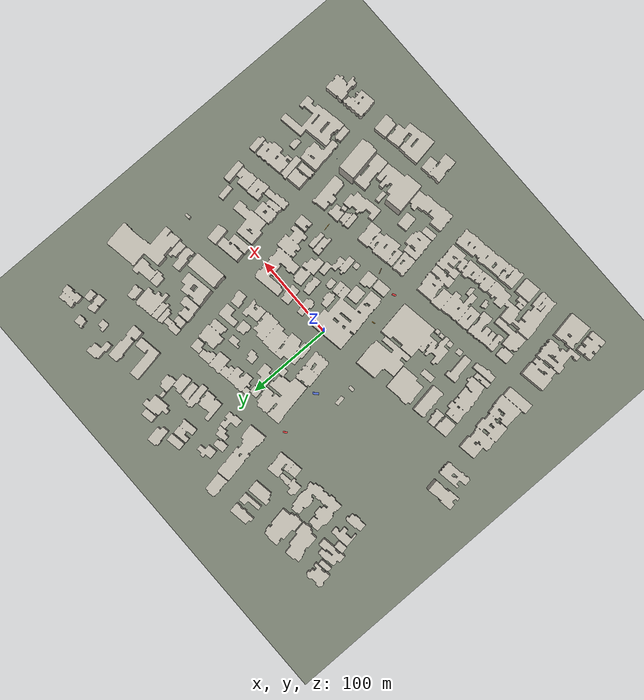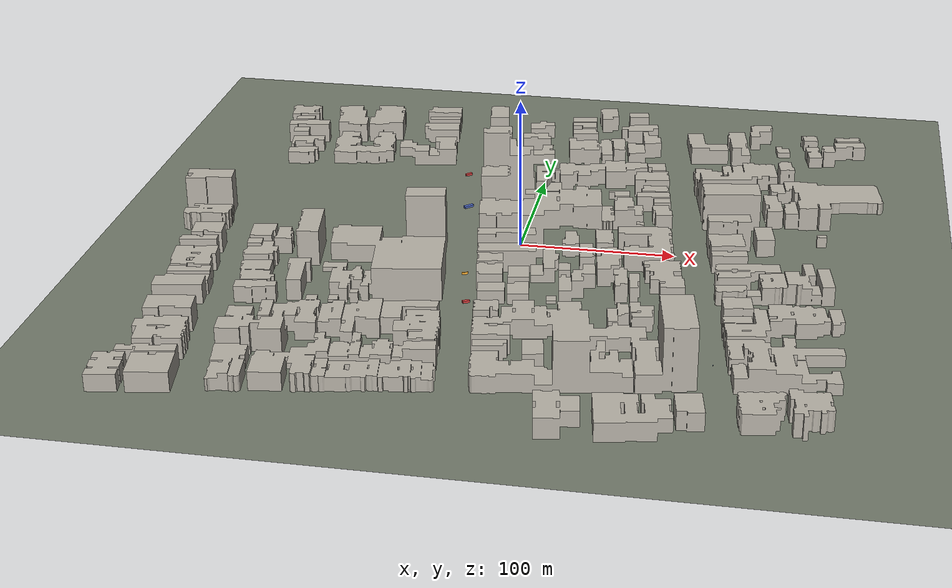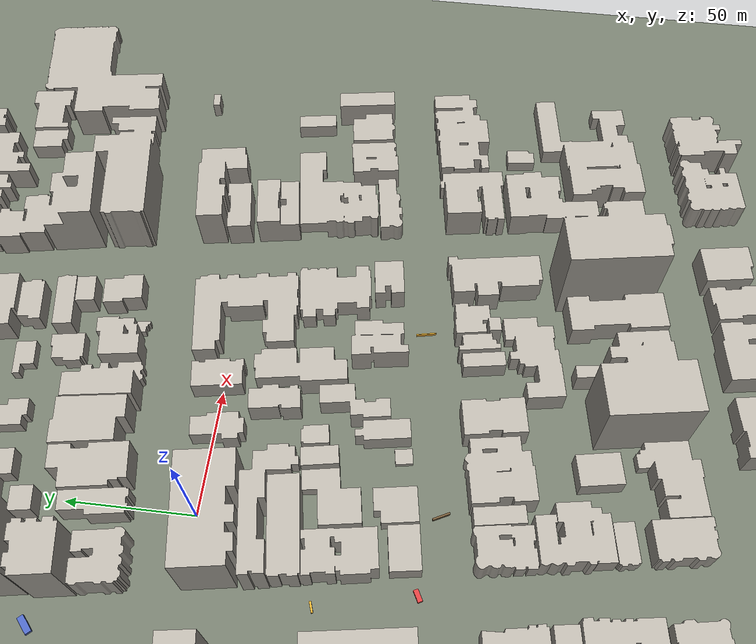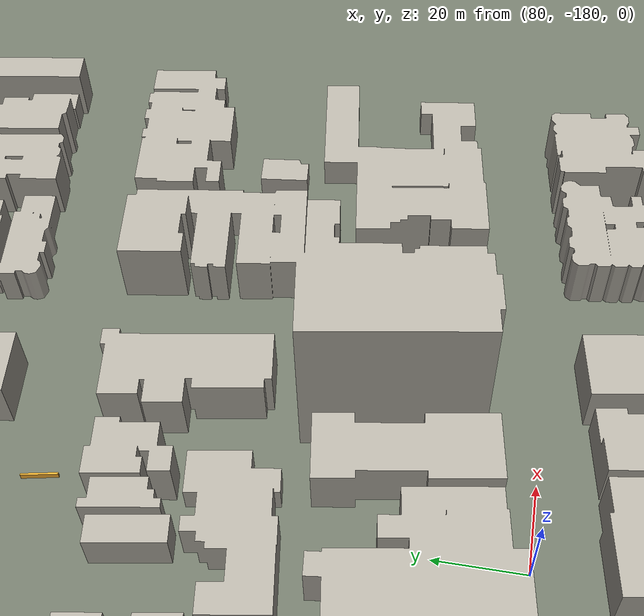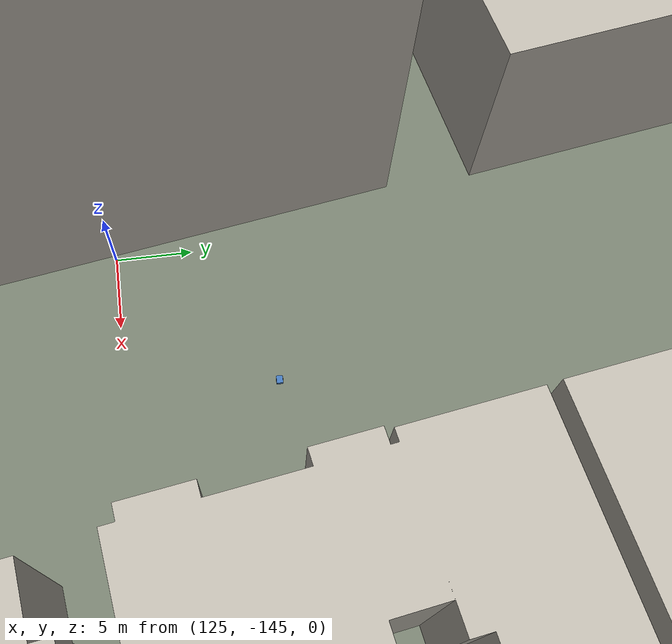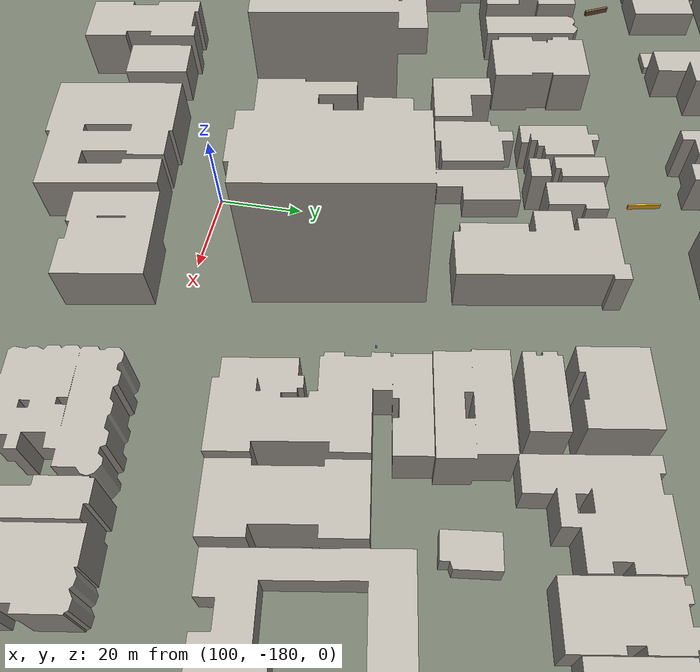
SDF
<?xml version="1.0" ?>
<sdf version="1.8">
  <world name="sanfrancisco_russian_hill">

    <physics name="1ms" type="ignored">
      <max_step_size>0.001</max_step_size>
      <real_time_factor>1.0</real_time_factor>
    </physics>

    <plugin filename="ignition-gazebo-physics-system"
            name="ignition::gazebo::systems::Physics"/>
    <plugin filename="ignition-gazebo-scene-broadcaster-system"
            name="ignition::gazebo::systems::SceneBroadcaster"/>
    <plugin filename="ignition-gazebo-user-commands-system"
            name="ignition::gazebo::systems::UserCommands"/>
    <!-- gpu_lidar produces nothing at all without this plugin. -->
    <plugin filename="ignition-gazebo-sensors-system"
            name="ignition::gazebo::systems::Sensors">
      <render_engine>ogre2</render_engine>
    </plugin>

    <!-- Documentary: lets a reader check the georeferencing claim against
         the OSM source. Nothing in the stack depends on it. -->
    <spherical_coordinates>
      <surface_model>EARTH_WGS84</surface_model>
      <world_frame_orientation>ENU</world_frame_orientation>
      <latitude_deg>37.801</latitude_deg>
      <longitude_deg>-122.419</longitude_deg>
      <elevation>70.0</elevation>
      <heading_deg>0</heading_deg>
    </spherical_coordinates>

    <scene>
      <ambient>0.35 0.35 0.38 1</ambient>
      <background>0.62 0.72 0.85 1</background>
      <shadows>false</shadows>
    </scene>

    <light type="directional" name="sun">
      <cast_shadows>false</cast_shadows>
      <pose>0 0 50 0 0 0</pose>
      <diffuse>0.95 0.93 0.88 1</diffuse>
      <specular>0.15 0.15 0.15 1</specular>
      <direction>-0.6 0.45 -0.65</direction>
    </light>

    <!-- A dim fill from the opposite side so shaded walls stay legible
         rather than going to flat black. Cheap: no shadows, no extra
         geometry pass. -->
    <light type="directional" name="fill">
      <cast_shadows>false</cast_shadows>
      <pose>0 0 50 0 0 0</pose>
      <diffuse>0.25 0.27 0.32 1</diffuse>
      <specular>0 0 0 1</specular>
      <direction>0.6 -0.45 -0.5</direction>
    </light>

    <model name="ground_plane">
      <static>true</static>
      <link name="link">
        <collision name="collision">
          <geometry><plane><normal>0 0 1</normal>
            <size>800 800</size></plane></geometry>
        </collision>
        <visual name="visual">
          <geometry><plane><normal>0 0 1</normal>
            <size>800 800</size></plane></geometry>
          <material>
            <ambient>0.35 0.37 0.33 1</ambient>
            <diffuse>0.45 0.48 0.42 1</diffuse>
          </material>
        </visual>
      </link>
    </model>

    <include>
      <uri>model://site_buildings</uri>
    </include>

    <include>
      <uri>model://roboto_bot</uri>
      <name>roboto_bot</name>
      <pose>134.9 -135.3 0 0 0 0.000000</pose>
    </include>

    <!-- Obstacles absent from OSM. Added to the WORLD ONLY: the
         prior costmap and occupancy grid are untouched, so the
         robot cannot know about these until it sees them. -->
    <model name="fence_panel_run_0">
      <static>true</static>
      <pose>85.051 -77.102 0.700 0 0 -1.372558</pose>
      <link name="link">
        <collision name="collision">
          <geometry><box><size>7.980 0.436 1.400</size></box></geometry>
        </collision>
        <visual name="visual">
          <geometry><box><size>7.980 0.436 1.400</size></box></geometry>
          <material>
            <ambient>0.90 0.60 0.10 1</ambient>
            <diffuse>1.00 0.70 0.20 1</diffuse>
          </material>
        </visual>
      </link>
    </model>
    <model name="fallen_tree_1">
      <static>true</static>
      <pose>9.984 -89.767 0.700 0 0 -1.110094</pose>
      <link name="link">
        <collision name="collision">
          <geometry><box><size>6.915 0.744 1.400</size></box></geometry>
        </collision>
        <visual name="visual">
          <geometry><box><size>6.915 0.744 1.400</size></box></geometry>
          <material>
            <ambient>0.35 0.25 0.12 1</ambient>
            <diffuse>0.45 0.35 0.22 1</diffuse>
          </material>
        </visual>
      </link>
    </model>
    <model name="parked_van_2">
      <static>true</static>
      <pose>-19.648 -84.048 0.700 0 0 3.622057</pose>
      <link name="link">
        <collision name="collision">
          <geometry><box><size>4.588 1.861 1.400</size></box></geometry>
        </collision>
        <visual name="visual">
          <geometry><box><size>4.588 1.861 1.400</size></box></geometry>
          <material>
            <ambient>0.75 0.15 0.15 1</ambient>
            <diffuse>0.85 0.25 0.25 1</diffuse>
          </material>
        </visual>
      </link>
    </model>
    <model name="fence_panel_run_3">
      <static>true</static>
      <pose>-27.807 -47.000 0.700 0 0 3.468942</pose>
      <link name="link">
        <collision name="collision">
          <geometry><box><size>4.069 0.762 1.400</size></box></geometry>
        </collision>
        <visual name="visual">
          <geometry><box><size>4.069 0.762 1.400</size></box></geometry>
          <material>
            <ambient>0.90 0.60 0.10 1</ambient>
            <diffuse>1.00 0.70 0.20 1</diffuse>
          </material>
        </visual>
      </link>
    </model>
    <model name="delivery_truck_4">
      <static>true</static>
      <pose>-45.136 51.532 0.700 0 0 3.884827</pose>
      <link name="link">
        <collision name="collision">
          <geometry><box><size>6.772 2.467 1.400</size></box></geometry>
        </collision>
        <visual name="visual">
          <geometry><box><size>6.772 2.467 1.400</size></box></geometry>
          <material>
            <ambient>0.20 0.30 0.65 1</ambient>
            <diffuse>0.30 0.40 0.75 1</diffuse>
          </material>
        </visual>
      </link>
    </model>
    <model name="parked_van_5">
      <static>true</static>
      <pose>-55.524 104.076 0.700 0 0 3.865987</pose>
      <link name="link">
        <collision name="collision">
          <geometry><box><size>4.803 1.814 1.400</size></box></geometry>
        </collision>
        <visual name="visual">
          <geometry><box><size>4.803 1.814 1.400</size></box></geometry>
          <material>
            <ambient>0.75 0.15 0.15 1</ambient>
            <diffuse>0.85 0.25 0.25 1</diffuse>
          </material>
        </visual>
      </link>
    </model>
  </world>
</sdf>

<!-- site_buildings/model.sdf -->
<sdf version="1.8">
  <model name="site_buildings">
    <static>true</static>
    <link name="link">
      <visual name="visual">
        <geometry><mesh><uri>meshes/buildings.obj</uri></mesh></geometry>
        <material>
          <ambient>0.62 0.60 0.56 1</ambient>
          <diffuse>0.72 0.70 0.66 1</diffuse>
          <specular>0.10 0.10 0.10 1</specular>
        </material>
      </visual>
      <collision name="c0">
        <pose>211.459 99.373 4.000 0 0 0.156840</pose>
        <geometry><box><size>39.560 30.591 8.000</size></box></geometry>
      </collision>
      <collision name="c1">
        <pose>185.775 105.556 4.000 0 0 1.716230</pose>
        <geometry><box><size>17.447 7.298 8.000</size></box></geometry>
      </collision>
      <collision name="c2">
        <pose>-175.502 -207.403 6.500 0 0 -1.402006</pose>
        <geometry><box><size>22.384 25.153 13.000</size></box></geometry>
      </collision>
      <collision name="c3">
        <pose>-201.664 -209.033 5.500 0 0 -2.982608</pose>
        <geometry><box><size>18.568 26.358 11.000</size></box></geometry>
      </collision>
      <collision name="c4">
        <pose>-178.064 -192.351 7.000 0 0 -2.968230</pose>
        <geometry><box><size>25.110 8.268 14.000</size></box></geometry>
      </collision>
      <collision name="c5">
        <pose>-196.344 -188.106 5.000 0 0 1.734147</pose>
        <geometry><box><size>6.389 14.358 10.000</size></box></geometry>
      </collision>
      <collision name="c6">
        <pose>191.258 -187.103 6.500 0 0 1.718981</pose>
        <geometry><box><size>19.528 7.616 13.000</size></box></geometry>
      </collision>
      <collision name="c7">
        <pose>163.342 -194.218 6.500 0 0 0.156268</pose>
        <geometry><box><size>22.168 7.325 13.000</size></box></geometry>
      </collision>
      <collision name="c8">
        <pose>164.644 -201.282 6.500 0 0 -2.982312</pose>
        <geometry><box><size>21.965 7.189 13.000</size></box></geometry>
      </collision>
      <collision name="c9">
        <pose>184.236 -192.419 7.500 0 0 -1.422097</pose>
        <geometry><box><size>28.481 7.844 15.000</size></box></geometry>
      </collision>
      <collision name="c10">
        <pose>198.977 -186.747 6.500 0 0 1.719249</pose>
        <geometry><box><size>21.697 7.761 13.000</size></box></geometry>
      </collision>
      <collision name="c11">
        <pose>164.723 -185.632 6.500 0 0 -2.988580</pose>
        <geometry><box><size>27.115 9.290 13.000</size></box></geometry>
      </collision>
      <collision name="c12">
        <pose>208.738 189.336 5.409 0 0 0.159674</pose>
        <geometry><box><size>17.920 7.602 10.818</size></box></geometry>
      </collision>
      <collision name="c13">
        <pose>145.962 197.332 5.000 0 0 0.160651</pose>
        <geometry><box><size>17.170 22.279 10.000</size></box></geometry>
      </collision>
      <collision name="c14">
        <pose>194.996 167.234 6.000 0 0 -1.410300</pose>
        <geometry><box><size>11.254 8.693 12.000</size></box></geometry>
      </collision>
      <collision name="c15">
        <pose>181.410 193.962 4.000 0 0 0.160385</pose>
        <geometry><box><size>10.799 10.449 8.000</size></box></geometry>
      </collision>
      <collision name="c16">
        <pose>130.813 172.444 4.630 0 0 -1.408550</pose>
        <geometry><box><size>42.651 12.870 9.261</size></box></geometry>
      </collision>
      <collision name="c17">
        <pose>184.903 168.526 4.000 0 0 1.731159</pose>
        <geometry><box><size>19.681 9.445 8.000</size></box></geometry>
      </collision>
      <collision name="c18">
        <pose>129.658 156.284 7.500 0 0 -1.408852</pose>
        <geometry><box><size>11.099 6.602 15.000</size></box></geometry>
      </collision>
      <collision name="c19">
        <pose>100.401 173.926 4.189 0 0 1.733142</pose>
        <geometry><box><size>30.209 11.393 8.377</size></box></geometry>
      </collision>
      <collision name="c20">
        <pose>119.849 159.510 5.500 0 0 -1.408668</pose>
        <geometry><box><size>11.022 7.411 11.000</size></box></geometry>
      </collision>
      <collision name="c21">
        <pose>113.184 158.387 5.500 0 0 1.732644</pose>
        <geometry><box><size>10.941 6.120 11.000</size></box></geometry>
      </collision>
      <collision name="c22">
        <pose>104.131 155.313 6.500 0 0 -2.980592</pose>
        <geometry><box><size>12.748 7.760 13.000</size></box></geometry>
      </collision>
      <collision name="c23">
        <pose>162.744 179.022 2.000 0 0 1.731443</pose>
        <geometry><box><size>10.807 8.964 4.000</size></box></geometry>
      </collision>
      <collision name="c24">
        <pose>210.134 181.277 5.000 0 0 0.159758</pose>
        <geometry><box><size>21.293 8.757 10.000</size></box></geometry>
      </collision>
      <collision name="c25">
        <pose>45.293 153.624 5.396 0 0 -1.409830</pose>
        <geometry><box><size>20.677 9.598 10.791</size></box></geometry>
      </collision>
      <collision name="c26">
        <pose>58.098 154.430 4.000 0 0 1.731167</pose>
        <geometry><box><size>19.922 12.015 8.000</size></box></geometry>
      </collision>
      <collision name="c27">
        <pose>36.136 150.958 4.500 0 0 -1.409782</pose>
        <geometry><box><size>28.745 9.337 9.000</size></box></geometry>
      </collision>
      <collision name="c28">
        <pose>26.555 145.624 6.000 0 0 0.159732</pose>
        <geometry><box><size>11.246 17.757 12.000</size></box></geometry>
      </collision>
      <collision name="c29">
        <pose>62.457 177.539 5.041 0 0 1.731138</pose>
        <geometry><box><size>7.069 4.013 10.082</size></box></geometry>
      </collision>
      <collision name="c30">
        <pose>55.381 186.335 5.000 0 0 0.159439</pose>
        <geometry><box><size>22.874 8.355 10.000</size></box></geometry>
      </collision>
      <collision name="c31">
        <pose>16.240 144.164 6.000 0 0 1.736226</pose>
        <geometry><box><size>15.837 10.751 12.000</size></box></geometry>
      </collision>
      <collision name="c32">
        <pose>68.540 165.462 5.500 0 0 -1.409947</pose>
        <geometry><box><size>15.883 12.156 11.000</size></box></geometry>
      </collision>
      <collision name="c33">
        <pose>31.713 210.015 5.500 0 0 -1.393572</pose>
        <geometry><box><size>21.016 12.900 11.000</size></box></geometry>
      </collision>
      <collision name="c34">
        <pose>-14.846 181.978 5.000 0 0 -1.391594</pose>
        <geometry><box><size>14.314 17.919 10.000</size></box></geometry>
      </collision>
      <collision name="c35">
        <pose>-43.773 165.692 3.969 0 0 -2.968375</pose>
        <geometry><box><size>16.430 14.516 7.939</size></box></geometry>
      </collision>
      <collision name="c36">
        <pose>-37.434 134.749 7.000 0 0 0.177727</pose>
        <geometry><box><size>22.044 20.702 14.000</size></box></geometry>
      </collision>
      <collision name="c37">
        <pose>-50.182 197.194 6.000 0 0 0.174072</pose>
        <geometry><box><size>14.180 22.698 12.000</size></box></geometry>
      </collision>
      <collision name="c38">
        <pose>-8.468 141.723 3.576 0 0 -1.422294</pose>
        <geometry><box><size>18.810 17.048 7.152</size></box></geometry>
      </collision>
      <collision name="c39">
        <pose>-41.483 151.637 6.500 0 0 0.172642</pose>
        <geometry><box><size>16.745 13.963 13.000</size></box></geometry>
      </collision>
      <collision name="c40">
        <pose>54.712 203.045 7.000 0 0 -2.971597</pose>
        <geometry><box><size>14.185 8.302 14.000</size></box></geometry>
      </collision>
      <collision name="c41">
        <pose>14.434 200.347 4.500 0 0 0.175326</pose>
        <geometry><box><size>17.771 8.840 9.000</size></box></geometry>
      </collision>
      <collision name="c42">
        <pose>-12.032 156.009 6.000 0 0 -2.990803</pose>
        <geometry><box><size>14.770 10.570 12.000</size></box></geometry>
      </collision>
      <collision name="c43">
        <pose>15.659 189.454 4.500 0 0 0.175089</pose>
        <geometry><box><size>17.414 9.662 9.000</size></box></geometry>
      </collision>
      <collision name="c44">
        <pose>17.581 180.329 4.000 0 0 0.175620</pose>
        <geometry><box><size>18.347 8.980 8.000</size></box></geometry>
      </collision>
      <collision name="c45">
        <pose>59.133 195.310 4.000 0 0 -2.971827</pose>
        <geometry><box><size>21.419 8.305 8.000</size></box></geometry>
      </collision>
      <collision name="c46">
        <pose>-46.035 179.534 2.581 0 0 0.172690</pose>
        <geometry><box><size>16.768 13.545 5.162</size></box></geometry>
      </collision>
      <collision name="c47">
        <pose>71.550 47.044 4.500 0 0 -1.411193</pose>
        <geometry><box><size>14.890 6.386 9.000</size></box></geometry>
      </collision>
      <collision name="c48">
        <pose>59.948 64.232 3.500 0 0 -1.409996</pose>
        <geometry><box><size>13.261 12.018 7.000</size></box></geometry>
      </collision>
      <collision name="c49">
        <pose>-34.406 96.657 5.411 0 0 -2.979550</pose>
        <geometry><box><size>16.452 16.200 10.822</size></box></geometry>
      </collision>
      <collision name="c50">
        <pose>74.009 37.211 2.000 0 0 -1.411116</pose>
        <geometry><box><size>5.324 4.789 4.000</size></box></geometry>
      </collision>
      <collision name="c51">
        <pose>51.296 44.054 3.192 0 0 1.720925</pose>
        <geometry><box><size>24.836 8.652 6.385</size></box></geometry>
      </collision>
      <collision name="c52">
        <pose>-16.224 96.307 5.032 0 0 1.734293</pose>
        <geometry><box><size>23.585 18.469 10.063</size></box></geometry>
      </collision>
      <collision name="c53">
        <pose>62.558 42.155 7.000 0 0 1.720564</pose>
        <geometry><box><size>15.530 13.052 14.000</size></box></geometry>
      </collision>
      <collision name="c54">
        <pose>-1.930 36.277 5.500 0 0 -1.408106</pose>
        <geometry><box><size>25.867 9.603 11.000</size></box></geometry>
      </collision>
      <collision name="c55">
        <pose>-16.916 29.489 7.000 0 0 1.733789</pose>
        <geometry><box><size>18.706 10.060 14.000</size></box></geometry>
      </collision>
      <collision name="c56">
        <pose>13.844 102.386 5.500 0 0 -1.407132</pose>
        <geometry><box><size>20.071 14.364 11.000</size></box></geometry>
      </collision>
      <collision name="c57">
        <pose>-26.785 27.888 7.500 0 0 -1.408027</pose>
        <geometry><box><size>18.688 9.939 15.000</size></box></geometry>
      </collision>
      <collision name="c58">
        <pose>-24.981 46.229 15.500 0 0 1.734543</pose>
        <geometry><box><size>16.961 19.316 31.000</size></box></geometry>
      </collision>
      <collision name="c59">
        <pose>22.854 45.746 8.000 0 0 -1.420657</pose>
        <geometry><box><size>24.504 9.191 16.000</size></box></geometry>
      </collision>
      <collision name="c60">
        <pose>-31.573 83.566 13.500 0 0 -2.979591</pose>
        <geometry><box><size>15.980 10.552 27.000</size></box></geometry>
      </collision>
      <collision name="c61">
        <pose>85.761 62.872 5.000 0 0 -2.981768</pose>
        <geometry><box><size>11.162 7.679 10.000</size></box></geometry>
      </collision>
      <collision name="c62">
        <pose>6.121 106.731 3.316 0 0 1.733760</pose>
        <geometry><box><size>7.170 6.390 6.632</size></box></geometry>
      </collision>
      <collision name="c63">
        <pose>32.290 44.935 8.000 0 0 -1.420962</pose>
        <geometry><box><size>26.730 9.245 16.000</size></box></geometry>
      </collision>
      <collision name="c64">
        <pose>79.377 69.629 5.500 0 0 0.159266</pose>
        <geometry><box><size>22.526 7.704 11.000</size></box></geometry>
      </collision>
      <collision name="c65">
        <pose>9.765 77.684 4.000 0 0 1.733677</pose>
        <geometry><box><size>14.146 10.102 8.000</size></box></geometry>
      </collision>
      <collision name="c66">
        <pose>36.097 108.090 5.500 0 0 -1.407312</pose>
        <geometry><box><size>14.165 10.512 11.000</size></box></geometry>
      </collision>
      <collision name="c67">
        <pose>76.958 113.896 6.000 0 0 0.161885</pose>
        <geometry><box><size>12.203 12.103 12.000</size></box></geometry>
      </collision>
      <collision name="c68">
        <pose>-1.008 99.422 5.720 0 0 0.162216</pose>
        <geometry><box><size>10.061 9.576 11.439</size></box></geometry>
      </collision>
      <collision name="c69">
        <pose>-26.748 58.656 27.500 0 0 -2.978982</pose>
        <geometry><box><size>17.375 7.650 55.000</size></box></geometry>
      </collision>
      <collision name="c70">
        <pose>41.877 44.952 8.500 0 0 1.720634</pose>
        <geometry><box><size>27.217 9.714 17.000</size></box></geometry>
      </collision>
      <collision name="c71">
        <pose>1.669 83.127 6.500 0 0 -1.408217</pose>
        <geometry><box><size>16.746 10.400 13.000</size></box></geometry>
      </collision>
      <collision name="c72">
        <pose>-20.798 71.742 17.500 0 0 0.162243</pose>
        <geometry><box><size>33.397 16.271 35.000</size></box></geometry>
      </collision>
      <collision name="c73">
        <pose>48.561 108.490 6.500 0 0 1.734402</pose>
        <geometry><box><size>19.591 14.207 13.000</size></box></geometry>
      </collision>
      <collision name="c74">
        <pose>14.342 41.639 7.000 0 0 1.733691</pose>
        <geometry><box><size>29.990 9.253 14.000</size></box></geometry>
      </collision>
      <collision name="c75">
        <pose>62.910 113.004 6.000 0 0 1.734428</pose>
        <geometry><box><size>12.826 15.026 12.000</size></box></geometry>
      </collision>
      <collision name="c76">
        <pose>87.452 47.661 5.000 0 0 -1.410579</pose>
        <geometry><box><size>15.664 12.331 10.000</size></box></geometry>
      </collision>
      <collision name="c77">
        <pose>26.051 104.583 5.000 0 0 -1.407660</pose>
        <geometry><box><size>17.861 10.448 10.000</size></box></geometry>
      </collision>
      <collision name="c78">
        <pose>6.453 38.001 7.000 0 0 -1.408129</pose>
        <geometry><box><size>25.341 7.503 14.000</size></box></geometry>
      </collision>
      <collision name="c79">
        <pose>78.846 84.112 4.500 0 0 -2.986116</pose>
        <geometry><box><size>18.281 9.296 9.000</size></box></geometry>
      </collision>
      <collision name="c80">
        <pose>75.187 101.722 6.000 0 0 -2.985844</pose>
        <geometry><box><size>22.080 8.282 12.000</size></box></geometry>
      </collision>
      <collision name="c81">
        <pose>54.712 80.819 2.500 0 0 0.155476</pose>
        <geometry><box><size>13.989 8.068 5.000</size></box></geometry>
      </collision>
      <collision name="c82">
        <pose>30.375 77.778 3.500 0 0 1.727498</pose>
        <geometry><box><size>12.117 10.764 7.000</size></box></geometry>
      </collision>
      <collision name="c83">
        <pose>75.757 92.971 6.500 0 0 0.156028</pose>
        <geometry><box><size>23.377 9.177 13.000</size></box></geometry>
      </collision>
      <collision name="c84">
        <pose>178.525 72.094 8.000 0 0 -1.419848</pose>
        <geometry><box><size>37.916 8.096 16.000</size></box></geometry>
      </collision>
      <collision name="c85">
        <pose>122.300 82.847 9.500 0 0 -2.965769</pose>
        <geometry><box><size>26.853 8.155 19.000</size></box></geometry>
      </collision>
      <collision name="c86">
        <pose>166.383 128.477 6.500 0 0 1.734638</pose>
        <geometry><box><size>15.202 9.984 13.000</size></box></geometry>
      </collision>
      <collision name="c87">
        <pose>159.971 64.999 6.500 0 0 -1.419806</pose>
        <geometry><box><size>26.212 10.690 13.000</size></box></geometry>
      </collision>
      <collision name="c88">
        <pose>116.928 92.171 7.000 0 0 -2.994620</pose>
        <geometry><box><size>19.466 10.318 14.000</size></box></geometry>
      </collision>
      <collision name="c89">
        <pose>125.929 120.661 5.000 0 0 -1.423282</pose>
        <geometry><box><size>18.239 6.156 10.000</size></box></geometry>
      </collision>
      <collision name="c90">
        <pose>141.840 117.780 6.000 0 0 1.718579</pose>
        <geometry><box><size>29.654 8.219 12.000</size></box></geometry>
      </collision>
      <collision name="c91">
        <pose>149.781 121.077 5.500 0 0 1.718747</pose>
        <geometry><box><size>25.660 8.458 11.000</size></box></geometry>
      </collision>
      <collision name="c92">
        <pose>118.739 121.932 3.415 0 0 0.147717</pose>
        <geometry><box><size>7.700 7.171 6.829</size></box></geometry>
      </collision>
      <collision name="c93">
        <pose>132.147 54.034 13.000 0 0 0.149913</pose>
        <geometry><box><size>37.747 17.693 26.000</size></box></geometry>
      </collision>
      <collision name="c94">
        <pose>110.164 112.403 6.000 0 0 -2.995000</pose>
        <geometry><box><size>11.482 9.055 12.000</size></box></geometry>
      </collision>
      <collision name="c95">
        <pose>161.742 100.234 4.000 0 0 1.716329</pose>
        <geometry><box><size>14.861 9.473 8.000</size></box></geometry>
      </collision>
      <collision name="c96">
        <pose>108.760 121.483 3.109 0 0 0.146364</pose>
        <geometry><box><size>12.185 9.199 6.218</size></box></geometry>
      </collision>
      <collision name="c97">
        <pose>111.940 101.718 6.500 0 0 0.146803</pose>
        <geometry><box><size>14.195 10.036 13.000</size></box></geometry>
      </collision>
      <collision name="c98">
        <pose>189.017 73.535 8.000 0 0 1.721744</pose>
        <geometry><box><size>38.208 13.083 16.000</size></box></geometry>
      </collision>
      <collision name="c99">
        <pose>174.426 102.091 5.000 0 0 1.716601</pose>
        <geometry><box><size>14.853 16.171 10.000</size></box></geometry>
      </collision>
      <collision name="c100">
        <pose>126.176 72.812 13.500 0 0 0.175981</pose>
        <geometry><box><size>30.952 12.966 27.000</size></box></geometry>
      </collision>
      <collision name="c101">
        <pose>133.598 120.238 5.000 0 0 1.718400</pose>
        <geometry><box><size>22.017 7.367 10.000</size></box></geometry>
      </collision>
      <collision name="c102">
        <pose>171.554 63.863 5.500 0 0 -1.420212</pose>
        <geometry><box><size>19.904 8.710 11.000</size></box></geometry>
      </collision>
      <collision name="c103">
        <pose>156.449 124.174 5.500 0 0 -1.408706</pose>
        <geometry><box><size>22.752 5.925 11.000</size></box></geometry>
      </collision>
      <collision name="c104">
        <pose>138.989 -47.435 7.000 0 0 0.157537</pose>
        <geometry><box><size>17.341 6.932 14.000</size></box></geometry>
      </collision>
      <collision name="c105">
        <pose>138.759 -32.472 6.000 0 0 -2.983796</pose>
        <geometry><box><size>21.454 7.353 12.000</size></box></geometry>
      </collision>
      <collision name="c106">
        <pose>133.401 18.968 10.500 0 0 0.157811</pose>
        <geometry><box><size>27.570 11.605 21.000</size></box></geometry>
      </collision>
      <collision name="c107">
        <pose>135.927 -13.354 6.000 0 0 -2.983564</pose>
        <geometry><box><size>22.575 7.862 12.000</size></box></geometry>
      </collision>
      <collision name="c108">
        <pose>160.818 -47.415 6.000 0 0 -1.411552</pose>
        <geometry><box><size>19.491 7.693 12.000</size></box></geometry>
      </collision>
      <collision name="c109">
        <pose>168.498 -45.800 6.000 0 0 -1.411712</pose>
        <geometry><box><size>19.505 7.990 12.000</size></box></geometry>
      </collision>
      <collision name="c110">
        <pose>139.921 -39.894 5.500 0 0 -2.983614</pose>
        <geometry><box><size>21.492 7.680 11.000</size></box></geometry>
      </collision>
      <collision name="c111">
        <pose>186.082 -17.679 3.500 0 0 1.732704</pose>
        <geometry><box><size>16.617 6.442 7.000</size></box></geometry>
      </collision>
      <collision name="c112">
        <pose>149.301 -21.142 3.226 0 0 -2.984116</pose>
        <geometry><box><size>38.528 11.712 6.453</size></box></geometry>
      </collision>
      <collision name="c113">
        <pose>153.466 -53.319 2.952 0 0 -2.984063</pose>
        <geometry><box><size>8.709 7.767 5.904</size></box></geometry>
      </collision>
      <collision name="c114">
        <pose>196.523 -39.200 6.500 0 0 -1.411560</pose>
        <geometry><box><size>24.726 7.670 13.000</size></box></geometry>
      </collision>
      <collision name="c115">
        <pose>156.278 19.106 6.000 0 0 1.732783</pose>
        <geometry><box><size>20.100 11.545 12.000</size></box></geometry>
      </collision>
      <collision name="c116">
        <pose>190.570 -45.273 3.500 0 0 1.729786</pose>
        <geometry><box><size>12.073 6.012 7.000</size></box></geometry>
      </collision>
      <collision name="c117">
        <pose>176.852 -44.748 7.000 0 0 1.729793</pose>
        <geometry><box><size>18.521 8.837 14.000</size></box></geometry>
      </collision>
      <collision name="c118">
        <pose>134.152 -4.830 7.500 0 0 0.157653</pose>
        <geometry><box><size>21.786 9.651 15.000</size></box></geometry>
      </collision>
      <collision name="c119">
        <pose>132.011 7.645 6.500 0 0 -2.983722</pose>
        <geometry><box><size>22.252 9.852 13.000</size></box></geometry>
      </collision>
      <collision name="c120">
        <pose>139.701 -56.397 4.758 0 0 0.157969</pose>
        <geometry><box><size>19.451 9.517 9.515</size></box></geometry>
      </collision>
      <collision name="c121">
        <pose>184.127 -43.140 5.500 0 0 1.730210</pose>
        <geometry><box><size>17.316 6.046 11.000</size></box></geometry>
      </collision>
      <collision name="c122">
        <pose>152.495 -125.069 5.500 0 0 -2.989658</pose>
        <geometry><box><size>22.040 7.941 11.000</size></box></geometry>
      </collision>
      <collision name="c123">
        <pose>167.127 -86.033 5.500 0 0 1.724228</pose>
        <geometry><box><size>20.813 7.253 11.000</size></box></geometry>
      </collision>
      <collision name="c124">
        <pose>150.836 -155.815 5.000 0 0 1.724233</pose>
        <geometry><box><size>17.000 7.876 10.000</size></box></geometry>
      </collision>
      <collision name="c125">
        <pose>146.030 -99.779 6.000 0 0 -2.989567</pose>
        <geometry><box><size>17.508 8.076 12.000</size></box></geometry>
      </collision>
      <collision name="c126">
        <pose>175.749 -145.043 6.500 0 0 -1.417693</pose>
        <geometry><box><size>30.756 14.614 13.000</size></box></geometry>
      </collision>
      <collision name="c127">
        <pose>147.374 -137.316 5.500 0 0 -1.417647</pose>
        <geometry><box><size>14.741 8.587 11.000</size></box></geometry>
      </collision>
      <collision name="c128">
        <pose>195.288 -80.711 4.500 0 0 1.724126</pose>
        <geometry><box><size>20.105 8.488 9.000</size></box></geometry>
      </collision>
      <collision name="c129">
        <pose>194.888 -144.696 3.618 0 0 1.723721</pose>
        <geometry><box><size>25.623 23.328 7.235</size></box></geometry>
      </collision>
      <collision name="c130">
        <pose>185.022 -83.780 5.000 0 0 -1.417770</pose>
        <geometry><box><size>22.956 12.741 10.000</size></box></geometry>
      </collision>
      <collision name="c131">
        <pose>160.980 -147.269 8.000 0 0 -1.417750</pose>
        <geometry><box><size>30.824 15.269 16.000</size></box></geometry>
      </collision>
      <collision name="c132">
        <pose>203.956 -79.240 4.000 0 0 -1.417285</pose>
        <geometry><box><size>19.065 7.590 8.000</size></box></geometry>
      </collision>
      <collision name="c133">
        <pose>194.736 -124.939 3.845 0 0 0.151840</pose>
        <geometry><box><size>29.069 13.514 7.690</size></box></geometry>
      </collision>
      <collision name="c134">
        <pose>150.283 -109.726 6.500 0 0 -2.989568</pose>
        <geometry><box><size>22.299 7.750 13.000</size></box></geometry>
      </collision>
      <collision name="c135">
        <pose>145.156 -86.710 8.000 0 0 1.723643</pose>
        <geometry><box><size>14.521 17.525 16.000</size></box></geometry>
      </collision>
      <collision name="c136">
        <pose>174.414 -83.126 5.500 0 0 1.723967</pose>
        <geometry><box><size>17.268 8.046 11.000</size></box></geometry>
      </collision>
      <collision name="c137">
        <pose>152.141 -117.231 6.500 0 0 -2.989488</pose>
        <geometry><box><size>22.724 7.656 13.000</size></box></geometry>
      </collision>
      <collision name="c138">
        <pose>160.085 -89.707 4.000 0 0 -1.417696</pose>
        <geometry><box><size>27.430 7.799 8.000</size></box></geometry>
      </collision>
      <collision name="c139">
        <pose>78.476 -98.374 6.000 0 0 1.736912</pose>
        <geometry><box><size>16.357 6.787 12.000</size></box></geometry>
      </collision>
      <collision name="c140">
        <pose>108.934 -89.506 6.000 0 0 1.735100</pose>
        <geometry><box><size>10.701 16.915 12.000</size></box></geometry>
      </collision>
      <collision name="c141">
        <pose>5.770 -156.598 3.500 0 0 -2.979265</pose>
        <geometry><box><size>15.858 7.886 7.000</size></box></geometry>
      </collision>
      <collision name="c142">
        <pose>98.372 -152.626 6.000 0 0 -1.407303</pose>
        <geometry><box><size>39.177 15.324 12.000</size></box></geometry>
      </collision>
      <collision name="c143">
        <pose>20.544 -110.926 6.500 0 0 1.734951</pose>
        <geometry><box><size>24.427 13.124 13.000</size></box></geometry>
      </collision>
      <collision name="c144">
        <pose>47.583 -106.281 6.000 0 0 -1.406428</pose>
        <geometry><box><size>24.275 14.152 12.000</size></box></geometry>
      </collision>
      <collision name="c145">
        <pose>75.862 -162.918 6.500 0 0 1.734751</pose>
        <geometry><box><size>25.585 18.000 13.000</size></box></geometry>
      </collision>
      <collision name="c146">
        <pose>2.130 -128.035 6.500 0 0 0.161082</pose>
        <geometry><box><size>18.193 7.898 13.000</size></box></geometry>
      </collision>
      <collision name="c147">
        <pose>78.232 -120.207 4.638 0 0 1.735770</pose>
        <geometry><box><size>19.249 13.659 9.275</size></box></geometry>
      </collision>
      <collision name="c148">
        <pose>-0.273 -119.949 4.500 0 0 0.162829</pose>
        <geometry><box><size>15.752 8.866 9.000</size></box></geometry>
      </collision>
      <collision name="c149">
        <pose>5.720 -137.880 6.500 0 0 -2.980866</pose>
        <geometry><box><size>22.737 12.694 13.000</size></box></geometry>
      </collision>
      <collision name="c150">
        <pose>8.469 -176.808 5.500 0 0 0.162123</pose>
        <geometry><box><size>15.330 22.645 11.000</size></box></geometry>
      </collision>
      <collision name="c151">
        <pose>108.820 -99.299 6.000 0 0 0.163663</pose>
        <geometry><box><size>17.790 8.596 12.000</size></box></geometry>
      </collision>
      <collision name="c152">
        <pose>19.886 -177.561 6.000 0 0 1.734530</pose>
        <geometry><box><size>15.093 6.986 12.000</size></box></geometry>
      </collision>
      <collision name="c153">
        <pose>56.057 -161.111 16.500 0 0 1.734212</pose>
        <geometry><box><size>35.542 20.507 33.000</size></box></geometry>
      </collision>
      <collision name="c154">
        <pose>10.406 -110.710 4.500 0 0 -1.406781</pose>
        <geometry><box><size>19.431 6.809 9.000</size></box></geometry>
      </collision>
      <collision name="c155">
        <pose>88.366 -163.309 5.000 0 0 1.734565</pose>
        <geometry><box><size>20.757 6.541 10.000</size></box></geometry>
      </collision>
      <collision name="c156">
        <pose>30.668 -108.972 4.500 0 0 1.735270</pose>
        <geometry><box><size>25.010 7.505 9.000</size></box></geometry>
      </collision>
      <collision name="c157">
        <pose>72.398 -100.887 4.500 0 0 1.737165</pose>
        <geometry><box><size>16.871 6.035 9.000</size></box></geometry>
      </collision>
      <collision name="c158">
        <pose>87.106 -104.022 6.000 0 0 0.163842</pose>
        <geometry><box><size>5.792 4.760 12.000</size></box></geometry>
      </collision>
      <collision name="c159">
        <pose>27.067 -176.348 6.000 0 0 -1.407204</pose>
        <geometry><box><size>15.151 7.581 12.000</size></box></geometry>
      </collision>
      <collision name="c160">
        <pose>64.930 -124.711 5.500 0 0 1.735296</pose>
        <geometry><box><size>14.689 14.069 11.000</size></box></geometry>
      </collision>
      <collision name="c161">
        <pose>34.145 -174.752 6.000 0 0 1.734164</pose>
        <geometry><box><size>17.167 6.900 12.000</size></box></geometry>
      </collision>
      <collision name="c162">
        <pose>7.085 -147.763 5.000 0 0 0.161012</pose>
        <geometry><box><size>20.156 7.250 10.000</size></box></geometry>
      </collision>
      <collision name="c163">
        <pose>92.644 -94.888 5.000 0 0 1.734924</pose>
        <geometry><box><size>13.700 8.127 10.000</size></box></geometry>
      </collision>
      <collision name="c164">
        <pose>85.266 -94.554 6.000 0 0 1.734812</pose>
        <geometry><box><size>12.092 6.311 12.000</size></box></geometry>
      </collision>
      <collision name="c165">
        <pose>42.138 -170.862 2.500 0 0 1.734053</pose>
        <geometry><box><size>20.770 10.137 5.000</size></box></geometry>
      </collision>
      <collision name="c166">
        <pose>115.191 -147.663 20.000 0 0 1.734196</pose>
        <geometry><box><size>40.511 19.481 40.000</size></box></geometry>
      </collision>
      <collision name="c167">
        <pose>112.809 -112.310 6.000 0 0 1.735345</pose>
        <geometry><box><size>18.403 14.176 12.000</size></box></geometry>
      </collision>
      <collision name="c168">
        <pose>37.434 -107.563 4.000 0 0 -1.406101</pose>
        <geometry><box><size>19.297 6.301 8.000</size></box></geometry>
      </collision>
      <collision name="c169">
        <pose>-2.550 -108.866 6.500 0 0 -2.979075</pose>
        <geometry><box><size>15.267 13.749 13.000</size></box></geometry>
      </collision>
      <collision name="c170">
        <pose>72.279 -59.631 6.500 0 0 -1.424181</pose>
        <geometry><box><size>22.395 8.290 13.000</size></box></geometry>
      </collision>
      <collision name="c171">
        <pose>61.630 -20.340 4.500 0 0 -1.406989</pose>
        <geometry><box><size>18.174 12.603 9.000</size></box></geometry>
      </collision>
      <collision name="c172">
        <pose>32.893 -2.009 4.500 0 0 -1.406582</pose>
        <geometry><box><size>20.450 10.873 9.000</size></box></geometry>
      </collision>
      <collision name="c173">
        <pose>-9.328 -61.060 6.500 0 0 0.163102</pose>
        <geometry><box><size>16.453 15.344 13.000</size></box></geometry>
      </collision>
      <collision name="c174">
        <pose>-3.364 -34.231 7.500 0 0 0.162954</pose>
        <geometry><box><size>37.019 11.843 15.000</size></box></geometry>
      </collision>
      <collision name="c175">
        <pose>54.633 1.904 5.000 0 0 -1.406700</pose>
        <geometry><box><size>20.417 11.268 10.000</size></box></geometry>
      </collision>
      <collision name="c176">
        <pose>-5.252 -23.774 10.500 0 0 -2.978911</pose>
        <geometry><box><size>37.234 9.418 21.000</size></box></geometry>
      </collision>
      <collision name="c177">
        <pose>-11.479 -47.573 7.000 0 0 -2.978976</pose>
        <geometry><box><size>16.106 11.978 14.000</size></box></geometry>
      </collision>
      <collision name="c178">
        <pose>95.509 -31.696 4.428 0 0 0.145038</pose>
        <geometry><box><size>23.235 15.128 8.856</size></box></geometry>
      </collision>
      <collision name="c179">
        <pose>69.923 -31.477 2.000 0 0 -1.408120</pose>
        <geometry><box><size>6.258 2.766 4.000</size></box></geometry>
      </collision>
      <collision name="c180">
        <pose>97.145 -43.092 5.000 0 0 -2.996553</pose>
        <geometry><box><size>12.224 7.899 10.000</size></box></geometry>
      </collision>
      <collision name="c181">
        <pose>-5.267 -77.656 4.500 0 0 0.153379</pose>
        <geometry><box><size>16.714 11.670 9.000</size></box></geometry>
      </collision>
      <collision name="c182">
        <pose>50.913 -45.723 5.000 0 0 -1.407201</pose>
        <geometry><box><size>13.750 7.585 10.000</size></box></geometry>
      </collision>
      <collision name="c183">
        <pose>82.199 -4.555 6.000 0 0 0.162499</pose>
        <geometry><box><size>34.434 41.938 12.000</size></box></geometry>
      </collision>
      <collision name="c184">
        <pose>45.465 -59.179 6.000 0 0 0.162485</pose>
        <geometry><box><size>7.553 15.385 12.000</size></box></geometry>
      </collision>
      <collision name="c185">
        <pose>80.773 -58.475 5.500 0 0 -1.424659</pose>
        <geometry><box><size>19.421 6.427 11.000</size></box></geometry>
      </collision>
      <collision name="c186">
        <pose>61.960 -38.796 6.000 0 0 -1.407044</pose>
        <geometry><box><size>18.362 14.128 12.000</size></box></geometry>
      </collision>
      <collision name="c187">
        <pose>104.002 -59.802 6.000 0 0 -2.996055</pose>
        <geometry><box><size>15.088 11.836 12.000</size></box></geometry>
      </collision>
      <collision name="c188">
        <pose>99.394 -49.788 5.000 0 0 0.145443</pose>
        <geometry><box><size>19.768 6.008 10.000</size></box></geometry>
      </collision>
      <collision name="c189">
        <pose>38.557 -64.776 4.500 0 0 1.734346</pose>
        <geometry><box><size>21.148 7.917 9.000</size></box></geometry>
      </collision>
      <collision name="c190">
        <pose>31.247 -73.649 1.000 0 0 -1.408519</pose>
        <geometry><box><size>6.761 6.051 2.000</size></box></geometry>
      </collision>
      <collision name="c191">
        <pose>7.477 -52.438 3.876 0 0 1.734035</pose>
        <geometry><box><size>16.055 13.404 7.753</size></box></geometry>
      </collision>
      <collision name="c192">
        <pose>10.543 -72.818 3.624 0 0 -1.407386</pose>
        <geometry><box><size>16.466 13.440 7.248</size></box></geometry>
      </collision>
      <collision name="c193">
        <pose>34.500 -39.286 3.500 0 0 1.734069</pose>
        <geometry><box><size>10.749 7.416 7.000</size></box></geometry>
      </collision>
      <collision name="c194">
        <pose>83.875 -210.042 6.000 0 0 1.734296</pose>
        <geometry><box><size>31.079 17.234 12.000</size></box></geometry>
      </collision>
      <collision name="c195">
        <pose>96.655 -207.844 6.000 0 0 1.734474</pose>
        <geometry><box><size>29.089 8.704 12.000</size></box></geometry>
      </collision>
      <collision name="c196">
        <pose>50.566 -213.610 6.500 0 0 -1.407545</pose>
        <geometry><box><size>29.104 14.621 13.000</size></box></geometry>
      </collision>
      <collision name="c197">
        <pose>62.355 -206.113 5.000 0 0 -1.407691</pose>
        <geometry><box><size>15.843 10.692 10.000</size></box></geometry>
      </collision>
      <collision name="c198">
        <pose>126.220 -197.671 6.000 0 0 1.733954</pose>
        <geometry><box><size>20.345 15.422 12.000</size></box></geometry>
      </collision>
      <collision name="c199">
        <pose>112.825 -200.979 4.500 0 0 1.734015</pose>
        <geometry><box><size>20.339 8.962 9.000</size></box></geometry>
      </collision>
      <collision name="c200">
        <pose>105.034 -206.580 6.000 0 0 -1.407431</pose>
        <geometry><box><size>28.871 8.238 12.000</size></box></geometry>
      </collision>
      <collision name="c201">
        <pose>-88.758 -127.480 6.000 0 0 1.721142</pose>
        <geometry><box><size>23.525 7.161 12.000</size></box></geometry>
      </collision>
      <collision name="c202">
        <pose>-38.702 -119.601 5.000 0 0 0.150067</pose>
        <geometry><box><size>20.255 7.836 10.000</size></box></geometry>
      </collision>
      <collision name="c203">
        <pose>-67.638 -167.164 5.000 0 0 1.721647</pose>
        <geometry><box><size>15.000 6.039 10.000</size></box></geometry>
      </collision>
      <collision name="c204">
        <pose>-40.081 -184.964 4.500 0 0 1.744413</pose>
        <geometry><box><size>18.973 5.954 9.000</size></box></geometry>
      </collision>
      <collision name="c205">
        <pose>-131.283 -132.430 6.000 0 0 -1.420357</pose>
        <geometry><box><size>19.336 7.215 12.000</size></box></geometry>
      </collision>
      <collision name="c206">
        <pose>-133.928 -200.307 5.500 0 0 -1.420488</pose>
        <geometry><box><size>17.625 5.628 11.000</size></box></geometry>
      </collision>
      <collision name="c207">
        <pose>-28.071 -183.267 4.513 0 0 -1.397077</pose>
        <geometry><box><size>19.733 5.915 9.025</size></box></geometry>
      </collision>
      <collision name="c208">
        <pose>-74.336 -124.336 6.000 0 0 -1.419909</pose>
        <geometry><box><size>20.924 6.895 12.000</size></box></geometry>
      </collision>
      <collision name="c209">
        <pose>-116.378 -129.034 5.500 0 0 -1.420681</pose>
        <geometry><box><size>17.343 6.981 11.000</size></box></geometry>
      </collision>
      <collision name="c210">
        <pose>-34.025 -184.332 5.000 0 0 1.744515</pose>
        <geometry><box><size>19.785 6.196 10.000</size></box></geometry>
      </collision>
      <collision name="c211">
        <pose>-144.551 -144.704 4.500 0 0 0.149190</pose>
        <geometry><box><size>17.477 12.542 9.000</size></box></geometry>
      </collision>
      <collision name="c212">
        <pose>-30.256 -164.336 7.000 0 0 0.150141</pose>
        <geometry><box><size>18.860 9.858 14.000</size></box></geometry>
      </collision>
      <collision name="c213">
        <pose>-140.423 -201.796 4.000 0 0 -1.420115</pose>
        <geometry><box><size>19.303 7.654 8.000</size></box></geometry>
      </collision>
      <collision name="c214">
        <pose>-72.018 -190.519 4.500 0 0 1.722652</pose>
        <geometry><box><size>18.706 11.593 9.000</size></box></geometry>
      </collision>
      <collision name="c215">
        <pose>-80.511 -132.096 5.000 0 0 -1.415998</pose>
        <geometry><box><size>35.427 7.799 10.000</size></box></geometry>
      </collision>
      <collision name="c216">
        <pose>-91.092 -193.606 6.000 0 0 -1.436051</pose>
        <geometry><box><size>20.585 11.855 12.000</size></box></geometry>
      </collision>
      <collision name="c217">
        <pose>-76.411 -168.028 4.500 0 0 -1.419937</pose>
        <geometry><box><size>16.944 11.572 9.000</size></box></geometry>
      </collision>
      <collision name="c218">
        <pose>-21.495 -182.029 3.788 0 0 1.744516</pose>
        <geometry><box><size>19.545 7.467 7.576</size></box></geometry>
      </collision>
      <collision name="c219">
        <pose>-130.865 -163.998 9.500 0 0 -2.992066</pose>
        <geometry><box><size>38.559 14.819 19.000</size></box></geometry>
      </collision>
      <collision name="c220">
        <pose>-52.084 -186.579 5.000 0 0 -1.419673</pose>
        <geometry><box><size>19.191 6.446 10.000</size></box></geometry>
      </collision>
      <collision name="c221">
        <pose>-60.813 -188.723 4.500 0 0 -1.419475</pose>
        <geometry><box><size>18.527 11.465 9.000</size></box></geometry>
      </collision>
      <collision name="c222">
        <pose>-38.980 -136.258 5.500 0 0 -2.991602</pose>
        <geometry><box><size>26.525 10.850 11.000</size></box></geometry>
      </collision>
      <collision name="c223">
        <pose>-30.663 -154.710 7.500 0 0 0.150147</pose>
        <geometry><box><size>16.430 9.305 15.000</size></box></geometry>
      </collision>
      <collision name="c224">
        <pose>-52.692 -163.186 5.000 0 0 -1.420035</pose>
        <geometry><box><size>18.413 12.043 10.000</size></box></geometry>
      </collision>
      <collision name="c225">
        <pose>-127.825 -199.879 5.000 0 0 1.721479</pose>
        <geometry><box><size>19.261 6.574 10.000</size></box></geometry>
      </collision>
      <collision name="c226">
        <pose>-36.324 -146.100 7.500 0 0 0.150229</pose>
        <geometry><box><size>26.589 9.415 15.000</size></box></geometry>
      </collision>
      <collision name="c227">
        <pose>-81.683 -191.784 5.000 0 0 0.148840</pose>
        <geometry><box><size>7.954 20.194 10.000</size></box></geometry>
      </collision>
      <collision name="c228">
        <pose>-37.091 -127.145 5.000 0 0 0.150114</pose>
        <geometry><box><size>21.366 7.569 10.000</size></box></geometry>
      </collision>
      <collision name="c229">
        <pose>-105.763 -132.269 6.000 0 0 -1.405071</pose>
        <geometry><box><size>28.471 12.892 12.000</size></box></geometry>
      </collision>
      <collision name="c230">
        <pose>-106.590 -195.700 6.000 0 0 1.721959</pose>
        <geometry><box><size>18.772 10.045 12.000</size></box></geometry>
      </collision>
      <collision name="c231">
        <pose>-118.755 -178.993 4.479 0 0 1.720467</pose>
        <geometry><box><size>5.197 7.874 8.959</size></box></geometry>
      </collision>
      <collision name="c232">
        <pose>-115.999 -197.128 6.000 0 0 1.721869</pose>
        <geometry><box><size>18.783 8.989 12.000</size></box></geometry>
      </collision>
      <collision name="c233">
        <pose>-40.673 -111.994 6.000 0 0 1.722134</pose>
        <geometry><box><size>8.353 20.281 12.000</size></box></geometry>
      </collision>
      <collision name="c234">
        <pose>-85.213 -170.113 6.000 0 0 1.721516</pose>
        <geometry><box><size>15.431 6.466 12.000</size></box></geometry>
      </collision>
      <collision name="c235">
        <pose>-116.369 -183.953 5.271 0 0 -2.992145</pose>
        <geometry><box><size>11.115 5.322 10.542</size></box></geometry>
      </collision>
      <collision name="c236">
        <pose>-137.708 -182.415 4.500 0 0 -2.992039</pose>
        <geometry><box><size>19.297 5.871 9.000</size></box></geometry>
      </collision>
      <collision name="c237">
        <pose>-114.743 -172.410 2.000 0 0 -2.991834</pose>
        <geometry><box><size>17.785 6.624 4.000</size></box></geometry>
      </collision>
      <collision name="c238">
        <pose>-147.912 -131.718 4.000 0 0 -2.991621</pose>
        <geometry><box><size>15.033 12.540 8.000</size></box></geometry>
      </collision>
      <collision name="c239">
        <pose>-56.680 -119.571 5.500 0 0 -2.990812</pose>
        <geometry><box><size>13.403 20.984 11.000</size></box></geometry>
      </collision>
      <collision name="c240">
        <pose>-66.722 -124.567 6.500 0 0 -1.419905</pose>
        <geometry><box><size>25.503 8.095 13.000</size></box></geometry>
      </collision>
      <collision name="c241">
        <pose>-138.034 -188.553 4.500 0 0 -2.992110</pose>
        <geometry><box><size>16.259 6.176 9.000</size></box></geometry>
      </collision>
      <collision name="c242">
        <pose>-100.432 -170.418 2.000 0 0 1.721464</pose>
        <geometry><box><size>18.432 10.929 4.000</size></box></geometry>
      </collision>
      <collision name="c243">
        <pose>-61.530 -166.200 4.000 0 0 -1.419645</pose>
        <geometry><box><size>15.089 6.333 8.000</size></box></geometry>
      </collision>
      <collision name="c244">
        <pose>-138.893 -175.933 4.500 0 0 -2.992185</pose>
        <geometry><box><size>19.698 7.298 9.000</size></box></geometry>
      </collision>
      <collision name="c245">
        <pose>-123.792 -130.584 5.000 0 0 1.720605</pose>
        <geometry><box><size>16.637 8.159 10.000</size></box></geometry>
      </collision>
      <collision name="c246">
        <pose>-95.693 -128.473 5.000 0 0 1.720825</pose>
        <geometry><box><size>23.624 6.858 10.000</size></box></geometry>
      </collision>
      <collision name="c247">
        <pose>-91.703 -170.232 5.000 0 0 -1.420125</pose>
        <geometry><box><size>17.132 6.403 10.000</size></box></geometry>
      </collision>
      <collision name="c248">
        <pose>-43.701 -161.350 3.500 0 0 -1.420096</pose>
        <geometry><box><size>14.069 6.291 7.000</size></box></geometry>
      </collision>
      <collision name="c249">
        <pose>-45.771 -187.044 4.500 0 0 0.164516</pose>
        <geometry><box><size>6.096 16.470 9.000</size></box></geometry>
      </collision>
      <collision name="c250">
        <pose>-187.559 -141.935 8.000 0 0 -2.980111</pose>
        <geometry><box><size>28.877 16.489 16.000</size></box></geometry>
      </collision>
      <collision name="c251">
        <pose>-185.798 -154.523 5.500 0 0 -2.975667</pose>
        <geometry><box><size>26.508 9.324 11.000</size></box></geometry>
      </collision>
      <collision name="c252">
        <pose>-185.147 -163.821 7.000 0 0 0.163655</pose>
        <geometry><box><size>31.455 9.280 14.000</size></box></geometry>
      </collision>
      <collision name="c253">
        <pose>-181.581 -175.251 7.000 0 0 -2.980573</pose>
        <geometry><box><size>29.308 14.552 14.000</size></box></geometry>
      </collision>
      <collision name="c254">
        <pose>-147.407 -102.732 5.500 0 0 0.151804</pose>
        <geometry><box><size>25.696 9.385 11.000</size></box></geometry>
      </collision>
      <collision name="c255">
        <pose>-94.916 -85.106 5.000 0 0 1.723702</pose>
        <geometry><box><size>23.769 6.490 10.000</size></box></geometry>
      </collision>
      <collision name="c256">
        <pose>-158.173 -53.126 5.000 0 0 0.152014</pose>
        <geometry><box><size>19.506 7.604 10.000</size></box></geometry>
      </collision>
      <collision name="c257">
        <pose>-150.350 -29.529 5.500 0 0 -2.989691</pose>
        <geometry><box><size>11.083 17.448 11.000</size></box></geometry>
      </collision>
      <collision name="c258">
        <pose>-113.546 -27.596 6.000 0 0 -1.418383</pose>
        <geometry><box><size>27.034 11.508 12.000</size></box></geometry>
      </collision>
      <collision name="c259">
        <pose>-151.939 -84.258 3.979 0 0 -2.989526</pose>
        <geometry><box><size>21.656 13.101 7.958</size></box></geometry>
      </collision>
      <collision name="c260">
        <pose>-89.691 -75.390 5.000 0 0 -1.417280</pose>
        <geometry><box><size>19.175 6.818 10.000</size></box></geometry>
      </collision>
      <collision name="c261">
        <pose>-64.189 -41.627 5.000 0 0 0.151990</pose>
        <geometry><box><size>40.562 15.695 10.000</size></box></geometry>
      </collision>
      <collision name="c262">
        <pose>-155.950 -74.773 4.000 0 0 -2.989367</pose>
        <geometry><box><size>18.700 6.884 8.000</size></box></geometry>
      </collision>
      <collision name="c263">
        <pose>-158.173 -60.913 6.000 0 0 -2.989442</pose>
        <geometry><box><size>19.174 7.794 12.000</size></box></geometry>
      </collision>
      <collision name="c264">
        <pose>-131.135 -34.929 12.000 0 0 -1.417453</pose>
        <geometry><box><size>33.739 14.407 24.000</size></box></geometry>
      </collision>
      <collision name="c265">
        <pose>-60.068 -11.804 19.500 0 0 -2.989645</pose>
        <geometry><box><size>25.530 13.241 39.000</size></box></geometry>
      </collision>
      <collision name="c266">
        <pose>-113.694 -96.746 1.000 0 0 0.164150</pose>
        <geometry><box><size>6.940 6.336 2.000</size></box></geometry>
      </collision>
      <collision name="c267">
        <pose>-110.448 -53.670 1.500 0 0 -2.989532</pose>
        <geometry><box><size>15.107 7.469 3.000</size></box></geometry>
      </collision>
      <collision name="c268">
        <pose>-156.782 -45.250 5.000 0 0 1.724466</pose>
        <geometry><box><size>7.555 7.153 10.000</size></box></geometry>
      </collision>
      <collision name="c269">
        <pose>-81.011 -92.667 5.744 0 0 -2.989540</pose>
        <geometry><box><size>4.911 4.638 11.487</size></box></geometry>
      </collision>
      <collision name="c270">
        <pose>-100.563 -94.666 1.000 0 0 1.723170</pose>
        <geometry><box><size>6.266 5.837 2.000</size></box></geometry>
      </collision>
      <collision name="c271">
        <pose>-97.427 -27.459 6.000 0 0 1.723478</pose>
        <geometry><box><size>28.970 20.411 12.000</size></box></geometry>
      </collision>
      <collision name="c272">
        <pose>-87.604 -93.422 3.382 0 0 -2.989311</pose>
        <geometry><box><size>5.195 4.593 6.763</size></box></geometry>
      </collision>
      <collision name="c273">
        <pose>-163.722 -31.638 6.500 0 0 -2.989360</pose>
        <geometry><box><size>15.452 17.162 13.000</size></box></geometry>
      </collision>
      <collision name="c274">
        <pose>-164.941 -46.432 6.000 0 0 -2.988884</pose>
        <geometry><box><size>9.343 7.671 12.000</size></box></geometry>
      </collision>
      <collision name="c275">
        <pose>-102.933 -76.980 4.500 0 0 -1.417761</pose>
        <geometry><box><size>22.475 6.882 9.000</size></box></geometry>
      </collision>
      <collision name="c276">
        <pose>-65.636 -26.635 5.106 0 0 0.152129</pose>
        <geometry><box><size>41.057 14.386 10.212</size></box></geometry>
      </collision>
      <collision name="c277">
        <pose>-152.855 -94.853 4.000 0 0 -2.989663</pose>
        <geometry><box><size>19.441 6.054 8.000</size></box></geometry>
      </collision>
      <collision name="c278">
        <pose>-125.860 -84.108 7.000 0 0 -1.417731</pose>
        <geometry><box><size>29.889 13.658 14.000</size></box></geometry>
      </collision>
      <collision name="c279">
        <pose>-83.301 -74.904 3.640 0 0 -1.417649</pose>
        <geometry><box><size>18.943 5.959 7.280</size></box></geometry>
      </collision>
      <collision name="c280">
        <pose>-157.275 -68.110 4.000 0 0 0.152786</pose>
        <geometry><box><size>19.266 6.705 8.000</size></box></geometry>
      </collision>
      <collision name="c281">
        <pose>-58.787 -68.615 11.000 0 0 0.151812</pose>
        <geometry><box><size>43.077 39.310 22.000</size></box></geometry>
      </collision>
      <collision name="c282">
        <pose>-198.878 -37.990 7.500 0 0 1.723835</pose>
        <geometry><box><size>15.319 19.524 15.000</size></box></geometry>
      </collision>
      <collision name="c283">
        <pose>-193.345 -90.917 6.000 0 0 -2.989278</pose>
        <geometry><box><size>26.628 7.805 12.000</size></box></geometry>
      </collision>
      <collision name="c284">
        <pose>-194.844 -83.008 6.500 0 0 0.152120</pose>
        <geometry><box><size>24.899 8.311 13.000</size></box></geometry>
      </collision>
      <collision name="c285">
        <pose>-198.083 -65.086 6.000 0 0 0.151823</pose>
        <geometry><box><size>27.120 11.714 12.000</size></box></geometry>
      </collision>
      <collision name="c286">
        <pose>-201.569 -49.362 6.500 0 0 -2.989251</pose>
        <geometry><box><size>23.994 6.389 13.000</size></box></geometry>
      </collision>
      <collision name="c287">
        <pose>-197.788 -75.097 6.000 0 0 -2.989802</pose>
        <geometry><box><size>24.653 8.214 12.000</size></box></geometry>
      </collision>
      <collision name="c288">
        <pose>-193.839 -109.420 6.500 0 0 0.152241</pose>
        <geometry><box><size>30.965 11.950 13.000</size></box></geometry>
      </collision>
      <collision name="c289">
        <pose>-192.623 -98.975 5.000 0 0 0.152262</pose>
        <geometry><box><size>27.668 8.345 10.000</size></box></geometry>
      </collision>
      <collision name="c290">
        <pose>-200.112 -55.927 4.000 0 0 0.152341</pose>
        <geometry><box><size>24.867 7.030 8.000</size></box></geometry>
      </collision>
      <collision name="c291">
        <pose>-215.861 18.331 13.500 0 0 -2.987796</pose>
        <geometry><box><size>31.017 15.687 27.000</size></box></geometry>
      </collision>
      <collision name="c292">
        <pose>-209.022 0.504 5.500 0 0 0.155791</pose>
        <geometry><box><size>26.087 7.959 11.000</size></box></geometry>
      </collision>
      <collision name="c293">
        <pose>-210.051 -8.304 6.000 0 0 0.154391</pose>
        <geometry><box><size>30.684 9.165 12.000</size></box></geometry>
      </collision>
      <collision name="c294">
        <pose>-106.664 136.086 3.500 0 0 1.739360</pose>
        <geometry><box><size>16.399 12.245 7.000</size></box></geometry>
      </collision>
      <collision name="c295">
        <pose>-77.856 131.166 6.000 0 0 -1.402057</pose>
        <geometry><box><size>23.321 15.350 12.000</size></box></geometry>
      </collision>
      <collision name="c296">
        <pose>-193.969 172.197 6.000 0 0 -2.986837</pose>
        <geometry><box><size>20.007 7.391 12.000</size></box></geometry>
      </collision>
      <collision name="c297">
        <pose>-91.956 196.342 5.500 0 0 0.154827</pose>
        <geometry><box><size>24.918 11.380 11.000</size></box></geometry>
      </collision>
      <collision name="c298">
        <pose>-184.387 148.317 7.000 0 0 -2.986250</pose>
        <geometry><box><size>29.303 8.692 14.000</size></box></geometry>
      </collision>
      <collision name="c299">
        <pose>-179.713 127.292 4.500 0 0 1.726966</pose>
        <geometry><box><size>16.135 22.739 9.000</size></box></geometry>
      </collision>
      <collision name="c300">
        <pose>-178.406 109.175 4.500 0 0 0.155374</pose>
        <geometry><box><size>20.742 11.140 9.000</size></box></geometry>
      </collision>
      <collision name="c301">
        <pose>-187.226 156.394 5.500 0 0 0.155422</pose>
        <geometry><box><size>21.448 8.170 11.000</size></box></geometry>
      </collision>
      <collision name="c302">
        <pose>-195.468 180.883 6.000 0 0 -2.986501</pose>
        <geometry><box><size>21.416 10.235 12.000</size></box></geometry>
      </collision>
      <collision name="c303">
        <pose>-155.724 167.860 7.000 0 0 1.798027</pose>
        <geometry><box><size>38.574 21.968 14.000</size></box></geometry>
      </collision>
      <collision name="c304">
        <pose>-130.755 171.980 7.000 0 0 1.726069</pose>
        <geometry><box><size>37.819 24.700 14.000</size></box></geometry>
      </collision>
      <collision name="c305">
        <pose>-81.935 186.183 2.388 0 0 0.155064</pose>
        <geometry><box><size>8.120 6.251 4.775</size></box></geometry>
      </collision>
      <collision name="c306">
        <pose>-93.528 122.892 5.247 0 0 1.739708</pose>
        <geometry><box><size>12.222 10.262 10.494</size></box></geometry>
      </collision>
      <collision name="c307">
        <pose>-187.923 138.943 6.000 0 0 0.154994</pose>
        <geometry><box><size>11.088 8.159 12.000</size></box></geometry>
      </collision>
      <collision name="c308">
        <pose>-88.288 179.515 5.670 0 0 0.154914</pose>
        <geometry><box><size>22.667 4.967 11.340</size></box></geometry>
      </collision>
      <collision name="c309">
        <pose>-84.968 124.740 3.552 0 0 1.739679</pose>
        <geometry><box><size>13.000 7.235 7.104</size></box></geometry>
      </collision>
      <collision name="c310">
        <pose>-192.243 164.803 5.403 0 0 0.155255</pose>
        <geometry><box><size>13.593 5.877 10.806</size></box></geometry>
      </collision>
      <collision name="c311">
        <pose>-88.050 165.946 5.000 0 0 -2.986906</pose>
        <geometry><box><size>25.545 13.487 10.000</size></box></geometry>
      </collision>
      <collision name="c312">
        <pose>-94.021 137.560 2.000 0 0 -2.974233</pose>
        <geometry><box><size>13.200 6.881 4.000</size></box></geometry>
      </collision>
      <collision name="c313">
        <pose>-137.444 130.380 4.500 0 0 0.155914</pose>
        <geometry><box><size>43.082 39.129 9.000</size></box></geometry>
      </collision>
      <collision name="c314">
        <pose>-68.262 36.747 2.500 0 0 1.712004</pose>
        <geometry><box><size>10.762 4.537 5.000</size></box></geometry>
      </collision>
      <collision name="c315">
        <pose>-66.712 18.514 1.500 0 0 -2.998113</pose>
        <geometry><box><size>6.445 3.802 3.000</size></box></geometry>
      </collision>
      <collision name="c316">
        <pose>193.056 30.564 3.779 0 0 -3.021860</pose>
        <geometry><box><size>6.228 3.086 7.558</size></box></geometry>
      </collision>
      <collision name="c317">
        <pose>-20.205 165.984 3.729 0 0 0.163965</pose>
        <geometry><box><size>13.331 9.282 7.458</size></box></geometry>
      </collision>
      <collision name="c318">
        <pose>11.550 155.628 5.179 0 0 1.743470</pose>
        <geometry><box><size>8.310 5.336 10.358</size></box></geometry>
      </collision>
      <collision name="c319">
        <pose>23.712 -26.064 3.696 0 0 1.711789</pose>
        <geometry><box><size>17.261 10.206 7.392</size></box></geometry>
      </collision>
      <collision name="c320">
        <pose>17.572 -43.997 2.788 0 0 -1.395519</pose>
        <geometry><box><size>14.408 8.136 5.576</size></box></geometry>
      </collision>
      <collision name="c321">
        <pose>25.170 -42.682 5.123 0 0 1.746074</pose>
        <geometry><box><size>14.309 7.286 10.246</size></box></geometry>
      </collision>
      <collision name="c322">
        <pose>70.901 -142.892 5.492 0 0 -1.448301</pose>
        <geometry><box><size>12.617 5.111 10.984</size></box></geometry>
      </collision>
      <collision name="c323">
        <pose>177.243 -110.711 2.750 0 0 1.688306</pose>
        <geometry><box><size>11.656 7.140 5.500</size></box></geometry>
      </collision>
      <collision name="c324">
        <pose>32.027 -146.588 4.448 0 0 1.747844</pose>
        <geometry><box><size>16.920 12.388 8.896</size></box></geometry>
      </collision>
      <collision name="c325">
        <pose>-3.184 63.044 4.904 0 0 -2.981101</pose>
        <geometry><box><size>9.390 8.514 9.808</size></box></geometry>
      </collision>
      <collision name="c326">
        <pose>89.749 -118.006 3.152 0 0 1.733115</pose>
        <geometry><box><size>19.790 9.729 6.305</size></box></geometry>
      </collision>
      <collision name="c327">
        <pose>-4.815 -7.750 15.000 0 0 0.160780</pose>
        <geometry><box><size>41.461 22.202 30.000</size></box></geometry>
      </collision>
      <collision name="c328">
        <pose>46.400 -21.990 5.500 0 0 -2.978837</pose>
        <geometry><box><size>10.092 19.869 11.000</size></box></geometry>
      </collision>
      <collision name="c329">
        <pose>-92.831 -151.888 3.616 0 0 -1.403182</pose>
        <geometry><box><size>9.358 6.142 7.232</size></box></geometry>
      </collision>
      <collision name="c330">
        <pose>-71.385 -149.179 3.536 0 0 1.738795</pose>
        <geometry><box><size>10.487 4.949 7.072</size></box></geometry>
      </collision>
      <collision name="c331">
        <pose>-132.455 -153.158 4.500 0 0 0.148959</pose>
        <geometry><box><size>38.454 7.770 9.000</size></box></geometry>
      </collision>
    </link>
  </model>
</sdf>

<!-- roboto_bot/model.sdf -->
<sdf version="1.8">
  <model name="roboto_bot">

    <link name="base_link">
      <pose>0 0 0.15 0 0 0</pose>
      <inertial>
        <pose>0.07 0 0 0 0 0</pose>
        <mass>15.0</mass>
        <!-- Solid box 0.5 x 0.4 x 0.2: I = m/12 * (a^2 + b^2) -->
        <inertia>
          <ixx>0.2500</ixx><ixy>0</ixy><ixz>0</ixz>
          <iyy>0.3625</iyy><iyz>0</iyz>
          <izz>0.5125</izz>
        </inertia>
      </inertial>
      <collision name="collision">
        <geometry><box><size>0.5 0.4 0.2</size></box></geometry>
      </collision>
      <visual name="visual">
        <geometry><box><size>0.5 0.4 0.2</size></box></geometry>
        <material>
          <ambient>0.20 0.35 0.55 1</ambient>
          <diffuse>0.25 0.45 0.70 1</diffuse>
        </material>
      </visual>

      <sensor name="gpu_lidar" type="gpu_lidar">
        <!-- Clear of the chassis: a sensor inside its own collision box
             returns range_min on every beam. -->
        <pose>0.15 0 0.15 0 0 0</pose>
        <topic>scan</topic>
        <update_rate>10</update_rate>
        <always_on>true</always_on>
        <visualize>true</visualize>
        <lidar>
          <scan>
            <horizontal>
              <samples>180</samples>
              <resolution>1</resolution>
              <min_angle>-2.356194490</min_angle>  <!-- -135 deg -->
              <max_angle>2.356194490</max_angle>   <!-- +135 deg, 270 FOV -->
            </horizontal>
            <vertical>
              <samples>1</samples>
              <min_angle>0</min_angle>
              <max_angle>0</max_angle>
            </vertical>
          </scan>
          <range>
            <min>0.15</min>
            <max>30.0</max>
            <resolution>0.01</resolution>
          </range>
          <noise>
            <type>gaussian</type>
            <mean>0.0</mean>
            <stddev>0.02</stddev>
          </noise>
        </lidar>
      </sensor>
    </link>

    <link name="wheel_left">
      <pose>0 0.2 0.10 0 0 0</pose>
      <inertial>
        <mass>1.0</mass>
        <!-- Cylinder r=0.10 h=0.05, spin axis = y.
             about axis: m r^2 / 2 ; about diameter: m/12 (3r^2 + h^2) -->
        <inertia>
          <ixx>0.002708</ixx><ixy>0</ixy><ixz>0</ixz>
          <iyy>0.005000</iyy><iyz>0</iyz>
          <izz>0.002708</izz>
        </inertia>
      </inertial>
      <collision name="collision">
        <pose>0 0 0 1.5707963 0 0</pose>
        <geometry><cylinder><radius>0.10</radius><length>0.05</length></cylinder></geometry>
        <surface>
          <friction><ode><mu>1.0</mu><mu2>1.0</mu2></ode></friction>
        </surface>
      </collision>
      <visual name="visual">
        <pose>0 0 0 1.5707963 0 0</pose>
        <geometry><cylinder><radius>0.10</radius><length>0.05</length></cylinder></geometry>
        <material>
          <ambient>0.08 0.08 0.08 1</ambient>
          <diffuse>0.15 0.15 0.15 1</diffuse>
        </material>
      </visual>
    </link>

    <link name="wheel_right">
      <pose>0 -0.2 0.10 0 0 0</pose>
      <inertial>
        <mass>1.0</mass>
        <inertia>
          <ixx>0.002708</ixx><ixy>0</ixy><ixz>0</ixz>
          <iyy>0.005000</iyy><iyz>0</iyz>
          <izz>0.002708</izz>
        </inertia>
      </inertial>
      <collision name="collision">
        <pose>0 0 0 1.5707963 0 0</pose>
        <geometry><cylinder><radius>0.10</radius><length>0.05</length></cylinder></geometry>
        <surface>
          <friction><ode><mu>1.0</mu><mu2>1.0</mu2></ode></friction>
        </surface>
      </collision>
      <visual name="visual">
        <pose>0 0 0 1.5707963 0 0</pose>
        <geometry><cylinder><radius>0.10</radius><length>0.05</length></cylinder></geometry>
        <material>
          <ambient>0.08 0.08 0.08 1</ambient>
          <diffuse>0.15 0.15 0.15 1</diffuse>
        </material>
      </visual>
    </link>

    <link name="caster">
      <pose>0.18 0 0.05 0 0 0</pose>
      <inertial>
        <mass>0.5</mass>
        <inertia>
          <ixx>0.0005</ixx><ixy>0</ixy><ixz>0</ixz>
          <iyy>0.0005</iyy><iyz>0</iyz>
          <izz>0.0005</izz>
        </inertia>
      </inertial>
      <collision name="collision">
        <geometry><sphere><radius>0.05</radius></sphere></geometry>
        <surface>
          <!-- Near-frictionless: a caster that grips fights the drive
               wheels and makes the robot veer under pure-forward commands. -->
          <friction><ode><mu>0.001</mu><mu2>0.001</mu2></ode></friction>
        </surface>
      </collision>
      <visual name="visual">
        <geometry><sphere><radius>0.05</radius></sphere></geometry>
        <material><ambient>0.3 0.3 0.3 1</ambient></material>
      </visual>
    </link>

    <joint name="joint_wheel_left" type="revolute">
      <parent>base_link</parent>
      <child>wheel_left</child>
      <axis>
        <xyz>0 1 0</xyz>
        <limit><lower>-1e16</lower><upper>1e16</upper></limit>
        <dynamics><damping>0.02</damping></dynamics>
      </axis>
    </joint>

    <joint name="joint_wheel_right" type="revolute">
      <parent>base_link</parent>
      <child>wheel_right</child>
      <axis>
        <xyz>0 1 0</xyz>
        <limit><lower>-1e16</lower><upper>1e16</upper></limit>
        <dynamics><damping>0.02</damping></dynamics>
      </axis>
    </joint>

    <joint name="joint_caster" type="ball">
      <parent>base_link</parent>
      <child>caster</child>
    </joint>

    <plugin filename="ignition-gazebo-diff-drive-system"
            name="ignition::gazebo::systems::DiffDrive">
      <left_joint>joint_wheel_left</left_joint>
      <right_joint>joint_wheel_right</right_joint>
      <!-- Must match OdomErrorModel.wheel_baseline_m in
           roboto_core/sim/odom_corruptor.py -->
      <wheel_separation>0.4</wheel_separation>
      <wheel_radius>0.10</wheel_radius>
      <max_linear_acceleration>1.0</max_linear_acceleration>
      <topic>cmd_vel</topic>
      <odom_topic>odom</odom_topic>
      <tf_topic>tf</tf_topic>
      <frame_id>odom</frame_id>
      <child_frame_id>base_link</child_frame_id>
      <odom_publish_frequency>50</odom_publish_frequency>
    </plugin>

    <plugin filename="ignition-gazebo-pose-publisher-system"
            name="ignition::gazebo::systems::PosePublisher">
      <publish_link_pose>false</publish_link_pose>
      <publish_model_pose>true</publish_model_pose>
      <publish_nested_model_pose>false</publish_nested_model_pose>
      <use_pose_vector_msg>true</use_pose_vector_msg>
      <update_frequency>50</update_frequency>
    </plugin>

    <plugin filename="ignition-gazebo-joint-state-publisher-system"
            name="ignition::gazebo::systems::JointStatePublisher">
      <joint_name>joint_wheel_left</joint_name>
      <joint_name>joint_wheel_right</joint_name>
    </plugin>

  </model>
</sdf>
